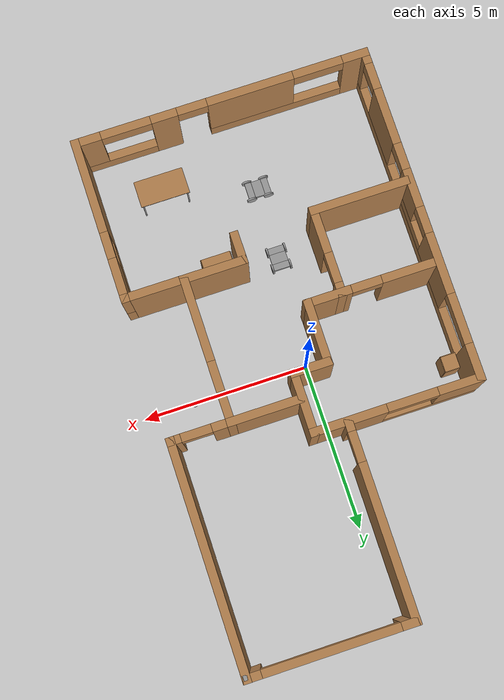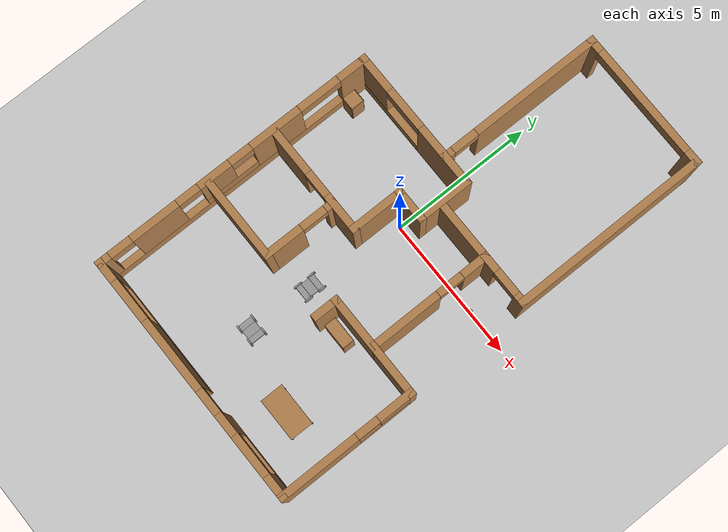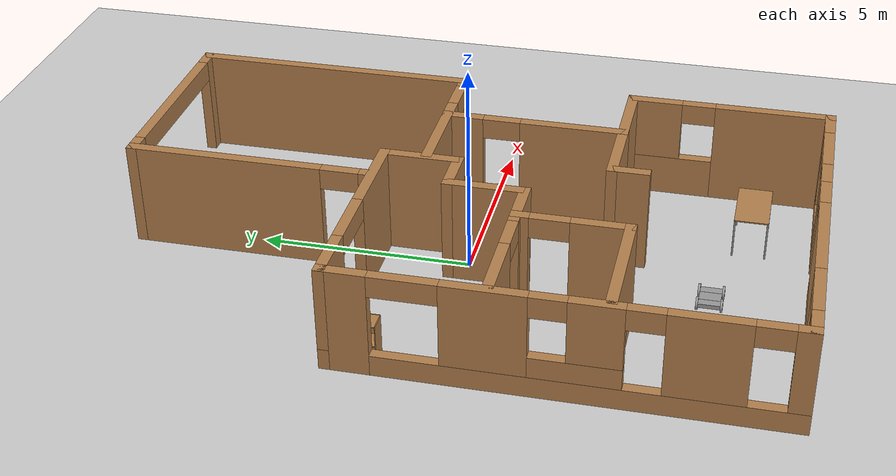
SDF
<sdf version="1.6">
 <world name="default">
  <plugin name="hello" filename="libhello.so"/>
  <light name="sun" type="directional">
   <pose>0 0 10 0 -0 0</pose>
   <diffuse>0.8 0.8 0.8 1</diffuse>
   <specular>0.1 0.1 0.1 1</specular>
   <attenuation>
    <range>1000</range>
    <constant>0.9</constant>
    <linear>0.01</linear>
    <quadratic>0.001</quadratic>
   </attenuation>
   <direction>-0.5 0.5 -1</direction>
  </light>
  <model name="ground_plane">
   <static>1</static>
   <link name="link">
    <collision name="collision">
     <geometry><plane><normal>0 0 1</normal><size>100 100</size></plane></geometry>
     <surface><friction><ode><mu>100</mu><mu2>50</mu2></ode></friction></surface>
    </collision>
    <visual name="visual">
     <cast_shadows>0</cast_shadows>
     <geometry><plane><normal>0 0 1</normal><size>100 100</size></plane></geometry>
     <material>
      <script><uri>file://media/materials/scripts/gazebo.material</uri><name>Gazebo/Grey</name></script>
     </material>
    </visual>
   </link>
  </model>
  <gravity>0 0 -9.8</gravity>
  <magnetic_field>6e-06 2.3e-05 -4.2e-05</magnetic_field>
  <atmosphere type="adiabatic"/>
  <physics name="default_physics" default="0" type="ode">
   <max_step_size>0.001</max_step_size>
   <real_time_factor>1</real_time_factor>
   <real_time_update_rate>1000</real_time_update_rate>
  </physics>
  <scene><ambient>0.4 0.4 0.4 1</ambient><background>0.7 0.7 0.7 1</background><shadows>1</shadows></scene>
  <spherical_coordinates>
   <surface_model>EARTH_WGS84</surface_model>
   <latitude_deg>0</latitude_deg>
   <longitude_deg>0</longitude_deg>
   <elevation>0</elevation>
   <heading_deg>0</heading_deg>
  </spherical_coordinates>
  <model name="mybuilding">
   <link name="Wall_0">
    <pose>1.95 7.875 0 0 -0 3.14159</pose>
    <visual name="Wall_0_Visual_0">
     <pose>-2.27407 0 1.25 0 -0 0</pose>
     <geometry><box><size>0.551856 0.25 2.5</size></box></geometry>
     <material>
      <script><uri>file://media/materials/scripts/gazebo.material</uri><name>Gazebo/Wood</name></script>
      <ambient>1 1 1 1</ambient>
     </material>
     <meta><layer>0</layer></meta>
    </visual>
    <collision name="Wall_0_Collision_0">
     <geometry><box><size>0.551856 0.25 2.5</size></box></geometry>
     <pose>-2.27407 0 1.25 0 -0 0</pose>
    </collision>
    <visual name="Wall_0_Visual_1">
     <pose>2.27593 0 1.25 0 -0 0</pose>
     <geometry><box><size>0.548144 0.25 2.5</size></box></geometry>
     <material>
      <script><uri>file://media/materials/scripts/gazebo.material</uri><name>Gazebo/Wood</name></script>
      <ambient>1 1 1 1</ambient>
     </material>
     <meta><layer>0</layer></meta>
    </visual>
    <collision name="Wall_0_Collision_1">
     <geometry><box><size>0.548144 0.25 2.5</size></box></geometry>
     <pose>2.27593 0 1.25 0 -0 0</pose>
    </collision>
    <visual name="Wall_0_Visual_2">
     <pose>0.001856 0 2.25 0 -0 0</pose>
     <geometry><box><size>4 0.25 0.5</size></box></geometry>
     <material>
      <script><uri>file://media/materials/scripts/gazebo.material</uri><name>Gazebo/Wood</name></script>
      <ambient>1 1 1 1</ambient>
     </material>
     <meta><layer>0</layer></meta>
    </visual>
    <collision name="Wall_0_Collision_2">
     <geometry><box><size>4 0.25 0.5</size></box></geometry>
     <pose>0.001856 0 2.25 0 -0 0</pose>
    </collision>
   </link>
   <link name="Wall_1">
    <pose>-0.475 5 0 0 0 -1.5708</pose>
    <visual name="Wall_1_Visual_0">
     <pose>-0.6625 0 1.25 0 -0 0</pose>
     <geometry><box><size>4.675 0.25 2.5</size></box></geometry>
     <material>
      <script><uri>file://media/materials/scripts/gazebo.material</uri><name>Gazebo/Wood</name></script>
      <ambient>1 1 1 1</ambient>
     </material>
     <meta><layer>0</layer></meta>
    </visual>
    <collision name="Wall_1_Collision_0">
     <geometry><box><size>4.675 0.25 2.5</size></box></geometry>
     <pose>-0.6625 0 1.25 0 -0 0</pose>
    </collision>
    <visual name="Wall_1_Visual_1">
     <pose>2.7875 0 1.25 0 -0 0</pose>
     <geometry><box><size>0.425 0.25 2.5</size></box></geometry>
     <material>
      <script><uri>file://media/materials/scripts/gazebo.material</uri><name>Gazebo/Wood</name></script>
      <ambient>1 1 1 1</ambient>
     </material>
     <meta><layer>0</layer></meta>
    </visual>
    <collision name="Wall_1_Collision_1">
     <geometry><box><size>0.425 0.25 2.5</size></box></geometry>
     <pose>2.7875 0 1.25 0 -0 0</pose>
    </collision>
    <visual name="Wall_1_Visual_2">
     <pose>2.125 0 2.25 0 -0 0</pose>
     <geometry><box><size>0.9 0.25 0.5</size></box></geometry>
     <material>
      <script><uri>file://media/materials/scripts/gazebo.material</uri><name>Gazebo/Wood</name></script>
      <ambient>1 1 1 1</ambient>
     </material>
     <meta><layer>0</layer></meta>
    </visual>
    <collision name="Wall_1_Collision_2">
     <geometry><box><size>0.9 0.25 0.5</size></box></geometry>
     <pose>2.125 0 2.25 0 -0 0</pose>
    </collision>
   </link>
   <link name="Wall_10">
    <pose>-4.375 -2.875 0 0 0 -1.5708</pose>
    <visual name="Wall_10_Visual_0">
     <pose>-4.56217 0 1.25 0 -0 0</pose>
     <geometry><box><size>1.12566 0.25 2.5</size></box></geometry>
     <material>
      <script><uri>file://media/materials/scripts/gazebo.material</uri><name>Gazebo/Wood</name></script>
      <ambient>1 1 1 1</ambient>
     </material>
     <meta><layer>0</layer></meta>
    </visual>
    <collision name="Wall_10_Collision_0">
     <geometry><box><size>1.12566 0.25 2.5</size></box></geometry>
     <pose>-4.56217 0 1.25 0 -0 0</pose>
    </collision>
    <visual name="Wall_10_Visual_1">
     <pose>0.562832 0 0.25 0 -0 0</pose>
     <geometry><box><size>9.12434 0.25 0.5</size></box></geometry>
     <material>
      <script><uri>file://media/materials/scripts/gazebo.material</uri><name>Gazebo/Wood</name></script>
      <ambient>1 1 1 1</ambient>
     </material>
     <meta><layer>0</layer></meta>
    </visual>
    <collision name="Wall_10_Collision_1">
     <geometry><box><size>9.12434 0.25 0.5</size></box></geometry>
     <pose>0.562832 0 0.25 0 -0 0</pose>
    </collision>
    <visual name="Wall_10_Visual_2">
     <pose>-1.57467 0 1.5 0 -0 0</pose>
     <geometry><box><size>1.84934 0.25 2</size></box></geometry>
     <material>
      <script><uri>file://media/materials/scripts/gazebo.material</uri><name>Gazebo/Wood</name></script>
      <ambient>1 1 1 1</ambient>
     </material>
     <meta><layer>0</layer></meta>
    </visual>
    <collision name="Wall_10_Collision_2">
     <geometry><box><size>1.84934 0.25 2</size></box></geometry>
     <pose>-1.57467 0 1.5 0 -0 0</pose>
    </collision>
    <visual name="Wall_10_Visual_3">
     <pose>2.98281 0 1.5 0 -0 0</pose>
     <geometry><box><size>1.72544 0.25 2</size></box></geometry>
     <material>
      <script><uri>file://media/materials/scripts/gazebo.material</uri><name>Gazebo/Wood</name></script>
      <ambient>1 1 1 1</ambient>
     </material>
     <meta><layer>0</layer></meta>
    </visual>
    <collision name="Wall_10_Collision_3">
     <geometry><box><size>1.72544 0.25 2</size></box></geometry>
     <pose>2.98281 0 1.5 0 -0 0</pose>
    </collision>
    <visual name="Wall_10_Visual_4">
     <pose>4.88526 0 1.5 0 -0 0</pose>
     <geometry><box><size>0.479475 0.25 2</size></box></geometry>
     <material>
      <script><uri>file://media/materials/scripts/gazebo.material</uri><name>Gazebo/Wood</name></script>
      <ambient>1 1 1 1</ambient>
     </material>
     <meta><layer>0</layer></meta>
    </visual>
    <collision name="Wall_10_Collision_4">
     <geometry><box><size>0.479475 0.25 2</size></box></geometry>
     <pose>4.88526 0 1.5 0 -0 0</pose>
    </collision>
    <visual name="Wall_10_Visual_5">
     <pose>0.335043 0 0.75 0 -0 0</pose>
     <geometry><box><size>1.97009 0.25 0.5</size></box></geometry>
     <material>
      <script><uri>file://media/materials/scripts/gazebo.material</uri><name>Gazebo/Wood</name></script>
      <ambient>1 1 1 1</ambient>
     </material>
     <meta><layer>0</layer></meta>
    </visual>
    <collision name="Wall_10_Collision_5">
     <geometry><box><size>1.97009 0.25 0.5</size></box></geometry>
     <pose>0.335043 0 0.75 0 -0 0</pose>
    </collision>
    <visual name="Wall_10_Visual_6">
     <pose>0.735043 0 1.75 0 -0 0</pose>
     <geometry><box><size>1.17009 0.25 1.5</size></box></geometry>
     <material>
      <script><uri>file://media/materials/scripts/gazebo.material</uri><name>Gazebo/Wood</name></script>
      <ambient>1 1 1 1</ambient>
     </material>
     <meta><layer>0</layer></meta>
    </visual>
    <collision name="Wall_10_Collision_6">
     <geometry><box><size>1.17009 0.25 1.5</size></box></geometry>
     <pose>0.735043 0 1.75 0 -0 0</pose>
    </collision>
    <visual name="Wall_10_Visual_7">
     <pose>-3.24934 0 2.25 0 -0 0</pose>
     <geometry><box><size>1.5 0.25 0.5</size></box></geometry>
     <material>
      <script><uri>file://media/materials/scripts/gazebo.material</uri><name>Gazebo/Wood</name></script>
      <ambient>1 1 1 1</ambient>
     </material>
     <meta><layer>0</layer></meta>
    </visual>
    <collision name="Wall_10_Collision_7">
     <geometry><box><size>1.5 0.25 0.5</size></box></geometry>
     <pose>-3.24934 0 2.25 0 -0 0</pose>
    </collision>
    <visual name="Wall_10_Visual_8">
     <pose>-0.25 0 2.25 0 -0 0</pose>
     <geometry><box><size>0.8 0.25 0.5</size></box></geometry>
     <material>
      <script><uri>file://media/materials/scripts/gazebo.material</uri><name>Gazebo/Wood</name></script>
      <ambient>1 1 1 1</ambient>
     </material>
     <meta><layer>0</layer></meta>
    </visual>
    <collision name="Wall_10_Collision_8">
     <geometry><box><size>0.8 0.25 0.5</size></box></geometry>
     <pose>-0.25 0 2.25 0 -0 0</pose>
    </collision>
    <visual name="Wall_10_Visual_9">
     <pose>4.24552 0 2.25 0 -0 0</pose>
     <geometry><box><size>0.8 0.25 0.5</size></box></geometry>
     <material>
      <script><uri>file://media/materials/scripts/gazebo.material</uri><name>Gazebo/Wood</name></script>
      <ambient>1 1 1 1</ambient>
     </material>
     <meta><layer>0</layer></meta>
    </visual>
    <collision name="Wall_10_Collision_9">
     <geometry><box><size>0.8 0.25 0.5</size></box></geometry>
     <pose>4.24552 0 2.25 0 -0 0</pose>
    </collision>
    <visual name="Wall_10_Visual_10">
     <pose>1.72009 0 2.25 0 -0 0</pose>
     <geometry><box><size>0.8 0.25 0.5</size></box></geometry>
     <material>
      <script><uri>file://media/materials/scripts/gazebo.material</uri><name>Gazebo/Wood</name></script>
      <ambient>1 1 1 1</ambient>
     </material>
     <meta><layer>0</layer></meta>
    </visual>
    <collision name="Wall_10_Collision_10">
     <geometry><box><size>0.8 0.25 0.5</size></box></geometry>
     <pose>1.72009 0 2.25 0 -0 0</pose>
    </collision>
   </link>
   <link name="Wall_11">
    <pose>0 -7.875 0 0 -0 0</pose>
    <visual name="Wall_11_Visual_0">
     <pose>-4.09506 0 1.25 0 -0 0</pose>
     <geometry><box><size>0.809873 0.25 2.5</size></box></geometry>
     <material>
      <script><uri>file://media/materials/scripts/gazebo.material</uri><name>Gazebo/Wood</name></script>
      <ambient>1 1 1 1</ambient>
     </material>
     <meta><layer>0</layer></meta>
    </visual>
    <collision name="Wall_11_Collision_0">
     <geometry><box><size>0.809873 0.25 2.5</size></box></geometry>
     <pose>-4.09506 0 1.25 0 -0 0</pose>
    </collision>
    <visual name="Wall_11_Visual_1">
     <pose>1.7214 0 1.25 0 -0 0</pose>
     <geometry><box><size>0.792805 0.25 2.5</size></box></geometry>
     <material>
      <script><uri>file://media/materials/scripts/gazebo.material</uri><name>Gazebo/Wood</name></script>
      <ambient>1 1 1 1</ambient>
     </material>
     <meta><layer>0</layer></meta>
    </visual>
    <collision name="Wall_11_Collision_1">
     <geometry><box><size>0.792805 0.25 2.5</size></box></geometry>
     <pose>1.7214 0 1.25 0 -0 0</pose>
    </collision>
    <visual name="Wall_11_Visual_2">
     <pose>-1.63256 0 0.25 0 -0 0</pose>
     <geometry><box><size>4.11513 0.25 0.5</size></box></geometry>
     <material>
      <script><uri>file://media/materials/scripts/gazebo.material</uri><name>Gazebo/Wood</name></script>
      <ambient>1 1 1 1</ambient>
     </material>
     <meta><layer>0</layer></meta>
    </visual>
    <collision name="Wall_11_Collision_2">
     <geometry><box><size>4.11513 0.25 0.5</size></box></geometry>
     <pose>-1.63256 0 0.25 0 -0 0</pose>
    </collision>
    <visual name="Wall_11_Visual_3">
     <pose>3.3089 0 0.25 0 -0 0</pose>
     <geometry><box><size>2.38219 0.25 0.5</size></box></geometry>
     <material>
      <script><uri>file://media/materials/scripts/gazebo.material</uri><name>Gazebo/Wood</name></script>
      <ambient>1 1 1 1</ambient>
     </material>
     <meta><layer>0</layer></meta>
    </visual>
    <collision name="Wall_11_Collision_3">
     <geometry><box><size>2.38219 0.25 0.5</size></box></geometry>
     <pose>3.3089 0 0.25 0 -0 0</pose>
    </collision>
    <visual name="Wall_11_Visual_4">
     <pose>-0.882564 0 1.5 0 -0 0</pose>
     <geometry><box><size>2.61513 0.25 2</size></box></geometry>
     <material>
      <script><uri>file://media/materials/scripts/gazebo.material</uri><name>Gazebo/Wood</name></script>
      <ambient>1 1 1 1</ambient>
     </material>
     <meta><layer>0</layer></meta>
    </visual>
    <collision name="Wall_11_Collision_4">
     <geometry><box><size>2.61513 0.25 2</size></box></geometry>
     <pose>-0.882564 0 1.5 0 -0 0</pose>
    </collision>
    <visual name="Wall_11_Visual_5">
     <pose>-0.882564 0 1.5 0 -0 0</pose>
     <geometry><box><size>2.61513 0.25 2</size></box></geometry>
     <material>
      <script><uri>file://media/materials/scripts/gazebo.material</uri><name>Gazebo/Wood</name></script>
      <ambient>1 1 1 1</ambient>
     </material>
     <meta><layer>0</layer></meta>
    </visual>
    <collision name="Wall_11_Collision_5">
     <geometry><box><size>2.61513 0.25 2</size></box></geometry>
     <pose>-0.882564 0 1.5 0 -0 0</pose>
    </collision>
    <visual name="Wall_11_Visual_6">
     <pose>4.0589 0 1.5 0 -0 0</pose>
     <geometry><box><size>0.882195 0.25 2</size></box></geometry>
     <material>
      <script><uri>file://media/materials/scripts/gazebo.material</uri><name>Gazebo/Wood</name></script>
      <ambient>1 1 1 1</ambient>
     </material>
     <meta><layer>0</layer></meta>
    </visual>
    <collision name="Wall_11_Collision_6">
     <geometry><box><size>0.882195 0.25 2</size></box></geometry>
     <pose>4.0589 0 1.5 0 -0 0</pose>
    </collision>
    <visual name="Wall_11_Visual_7">
     <pose>-2.94013 0 2.25 0 -0 0</pose>
     <geometry><box><size>1.5 0.25 0.5</size></box></geometry>
     <material>
      <script><uri>file://media/materials/scripts/gazebo.material</uri><name>Gazebo/Wood</name></script>
      <ambient>1 1 1 1</ambient>
     </material>
     <meta><layer>0</layer></meta>
    </visual>
    <collision name="Wall_11_Collision_7">
     <geometry><box><size>1.5 0.25 0.5</size></box></geometry>
     <pose>-2.94013 0 2.25 0 -0 0</pose>
    </collision>
    <visual name="Wall_11_Visual_8">
     <pose>2.86781 0 2.25 0 -0 0</pose>
     <geometry><box><size>1.5 0.25 0.5</size></box></geometry>
     <material>
      <script><uri>file://media/materials/scripts/gazebo.material</uri><name>Gazebo/Wood</name></script>
      <ambient>1 1 1 1</ambient>
     </material>
     <meta><layer>0</layer></meta>
    </visual>
    <collision name="Wall_11_Collision_8">
     <geometry><box><size>1.5 0.25 0.5</size></box></geometry>
     <pose>2.86781 0 2.25 0 -0 0</pose>
    </collision>
    <visual name="Wall_11_Visual_9">
     <pose>0.875 0 2.25 0 -0 0</pose>
     <geometry><box><size>0.9 0.25 0.5</size></box></geometry>
     <material>
      <script><uri>file://media/materials/scripts/gazebo.material</uri><name>Gazebo/Wood</name></script>
      <ambient>1 1 1 1</ambient>
     </material>
     <meta><layer>0</layer></meta>
    </visual>
    <collision name="Wall_11_Collision_9">
     <geometry><box><size>0.9 0.25 0.5</size></box></geometry>
     <pose>0.875 0 2.25 0 -0 0</pose>
    </collision>
    <visual name="Wall_11_Visual_10">
     <pose>0.875 0 2.25 0 -0 0</pose>
     <geometry><box><size>0.9 0.25 0.5</size></box></geometry>
     <material>
      <script><uri>file://media/materials/scripts/gazebo.material</uri><name>Gazebo/Wood</name></script>
      <ambient>1 1 1 1</ambient>
     </material>
     <meta><layer>0</layer></meta>
    </visual>
    <collision name="Wall_11_Collision_10">
     <geometry><box><size>0.9 0.25 0.5</size></box></geometry>
     <pose>0.875 0 2.25 0 -0 0</pose>
    </collision>
   </link>
   <link name="Wall_12">
    <pose>4.375 -5.5 0 0 -0 1.5708</pose>
    <visual name="Wall_12_Visual_0">
     <pose>-1.06859 0 1.25 0 -0 0</pose>
     <geometry><box><size>2.86282 0.25 2.5</size></box></geometry>
     <material>
      <script><uri>file://media/materials/scripts/gazebo.material</uri><name>Gazebo/Wood</name></script>
      <ambient>1 1 1 1</ambient>
     </material>
     <meta><layer>0</layer></meta>
    </visual>
    <collision name="Wall_12_Collision_0">
     <geometry><box><size>2.86282 0.25 2.5</size></box></geometry>
     <pose>-1.06859 0 1.25 0 -0 0</pose>
    </collision>
    <visual name="Wall_12_Visual_1">
     <pose>1.43141 0 0.5 0 -0 0</pose>
     <geometry><box><size>2.13718 0.25 1</size></box></geometry>
     <material>
      <script><uri>file://media/materials/scripts/gazebo.material</uri><name>Gazebo/Wood</name></script>
      <ambient>1 1 1 1</ambient>
     </material>
     <meta><layer>0</layer></meta>
    </visual>
    <collision name="Wall_12_Collision_1">
     <geometry><box><size>2.13718 0.25 1</size></box></geometry>
     <pose>1.43141 0 0.5 0 -0 0</pose>
    </collision>
    <visual name="Wall_12_Visual_2">
     <pose>1.83141 0 1.75 0 -0 0</pose>
     <geometry><box><size>1.33718 0.25 1.5</size></box></geometry>
     <material>
      <script><uri>file://media/materials/scripts/gazebo.material</uri><name>Gazebo/Wood</name></script>
      <ambient>1 1 1 1</ambient>
     </material>
     <meta><layer>0</layer></meta>
    </visual>
    <collision name="Wall_12_Collision_2">
     <geometry><box><size>1.33718 0.25 1.5</size></box></geometry>
     <pose>1.83141 0 1.75 0 -0 0</pose>
    </collision>
    <visual name="Wall_12_Visual_3">
     <pose>0.762824 0 2.25 0 -0 0</pose>
     <geometry><box><size>0.8 0.25 0.5</size></box></geometry>
     <material>
      <script><uri>file://media/materials/scripts/gazebo.material</uri><name>Gazebo/Wood</name></script>
      <ambient>1 1 1 1</ambient>
     </material>
     <meta><layer>0</layer></meta>
    </visual>
    <collision name="Wall_12_Collision_3">
     <geometry><box><size>0.8 0.25 0.5</size></box></geometry>
     <pose>0.762824 0 2.25 0 -0 0</pose>
    </collision>
   </link>
   <link name="Wall_13">
    <collision name="Wall_13_Collision">
     <geometry><box><size>2 0.25 2.5</size></box></geometry>
     <pose>0 0 1.25 0 -0 0</pose>
    </collision>
    <visual name="Wall_13_Visual">
     <pose>0 0 1.25 0 -0 0</pose>
     <geometry><box><size>2 0.25 2.5</size></box></geometry>
     <material>
      <script><uri>file://media/materials/scripts/gazebo.material</uri><name>Gazebo/Wood</name></script>
      <ambient>1 1 1 1</ambient>
     </material>
     <meta><layer>0</layer></meta>
    </visual>
    <pose>3.5 -3.125 0 0 -0 3.14159</pose>
   </link>
   <link name="Wall_14">
    <pose>2.625 -1 0 0 -0 1.5708</pose>
    <visual name="Wall_14_Visual_0">
     <pose>-0.957655 0 1.25 0 -0 0</pose>
     <geometry><box><size>2.58469 0.25 2.5</size></box></geometry>
     <material>
      <script><uri>file://media/materials/scripts/gazebo.material</uri><name>Gazebo/Wood</name></script>
      <ambient>1 1 1 1</ambient>
     </material>
     <meta><layer>0</layer></meta>
    </visual>
    <collision name="Wall_14_Collision_0">
     <geometry><box><size>2.58469 0.25 2.5</size></box></geometry>
     <pose>-0.957655 0 1.25 0 -0 0</pose>
    </collision>
    <visual name="Wall_14_Visual_1">
     <pose>1.74235 0 1.25 0 -0 0</pose>
     <geometry><box><size>1.01531 0.25 2.5</size></box></geometry>
     <material>
      <script><uri>file://media/materials/scripts/gazebo.material</uri><name>Gazebo/Wood</name></script>
      <ambient>1 1 1 1</ambient>
     </material>
     <meta><layer>0</layer></meta>
    </visual>
    <collision name="Wall_14_Collision_1">
     <geometry><box><size>1.01531 0.25 2.5</size></box></geometry>
     <pose>1.74235 0 1.25 0 -0 0</pose>
    </collision>
    <visual name="Wall_14_Visual_2">
     <pose>0.78469 0 2.25 0 -0 0</pose>
     <geometry><box><size>0.9 0.25 0.5</size></box></geometry>
     <material>
      <script><uri>file://media/materials/scripts/gazebo.material</uri><name>Gazebo/Wood</name></script>
      <ambient>1 1 1 1</ambient>
     </material>
     <meta><layer>0</layer></meta>
    </visual>
    <collision name="Wall_14_Collision_2">
     <geometry><box><size>0.9 0.25 0.5</size></box></geometry>
     <pose>0.78469 0 2.25 0 -0 0</pose>
    </collision>
   </link>
   <link name="Wall_153">
    <pose>-1.475 -2.625 0 0 0 -1.5708</pose>
    <visual name="Wall_153_Visual_0">
     <pose>-1.1625 0 1.25 0 -0 0</pose>
     <geometry><box><size>0.425 0.25 2.5</size></box></geometry>
     <material>
      <script><uri>file://media/materials/scripts/gazebo.material</uri><name>Gazebo/Wood</name></script>
      <ambient>1 1 1 1</ambient>
     </material>
     <meta><layer>0</layer></meta>
    </visual>
    <collision name="Wall_153_Collision_0">
     <geometry><box><size>0.425 0.25 2.5</size></box></geometry>
     <pose>-1.1625 0 1.25 0 -0 0</pose>
    </collision>
    <visual name="Wall_153_Visual_1">
     <pose>0.6625 0 1.25 0 -0 0</pose>
     <geometry><box><size>1.425 0.25 2.5</size></box></geometry>
     <material>
      <script><uri>file://media/materials/scripts/gazebo.material</uri><name>Gazebo/Wood</name></script>
      <ambient>1 1 1 1</ambient>
     </material>
     <meta><layer>0</layer></meta>
    </visual>
    <collision name="Wall_153_Collision_1">
     <geometry><box><size>1.425 0.25 2.5</size></box></geometry>
     <pose>0.6625 0 1.25 0 -0 0</pose>
    </collision>
    <visual name="Wall_153_Visual_2">
     <pose>-0.5 0 2.25 0 -0 0</pose>
     <geometry><box><size>0.9 0.25 0.5</size></box></geometry>
     <material>
      <script><uri>file://media/materials/scripts/gazebo.material</uri><name>Gazebo/Wood</name></script>
      <ambient>1 1 1 1</ambient>
     </material>
     <meta><layer>0</layer></meta>
    </visual>
    <collision name="Wall_153_Collision_2">
     <geometry><box><size>0.9 0.25 0.5</size></box></geometry>
     <pose>-0.5 0 2.25 0 -0 0</pose>
    </collision>
   </link>
   <link name="Wall_154">
    <collision name="Wall_154_Collision">
     <geometry><box><size>3 0.25 2.5</size></box></geometry>
     <pose>0 0 1.25 0 -0 0</pose>
    </collision>
    <visual name="Wall_154_Visual">
     <pose>0 0 1.25 0 -0 0</pose>
     <geometry><box><size>3 0.25 2.5</size></box></geometry>
     <material>
      <script><uri>file://media/materials/scripts/gazebo.material</uri><name>Gazebo/Wood</name></script>
      <ambient>1 1 1 1</ambient>
     </material>
     <meta><layer>0</layer></meta>
    </visual>
    <pose>-2.85 -3.875 0 0 -0 3.14159</pose>
   </link>
   <link name="Wall_156">
    <collision name="Wall_156_Collision">
     <geometry><box><size>2 0.25 2.5</size></box></geometry>
     <pose>0 0 1.25 0 -0 0</pose>
    </collision>
    <visual name="Wall_156_Visual">
     <pose>0 0 1.25 0 -0 0</pose>
     <geometry><box><size>2 0.25 2.5</size></box></geometry>
     <material>
      <script><uri>file://media/materials/scripts/gazebo.material</uri><name>Gazebo/Wood</name></script>
      <ambient>1 1 1 1</ambient>
     </material>
     <meta><layer>0</layer></meta>
    </visual>
    <pose>1.75 -3.125 0 0 -0 3.14159</pose>
   </link>
   <link name="Wall_157">
    <collision name="Wall_157_Collision">
     <geometry><box><size>1 0.25 2.5</size></box></geometry>
     <pose>0 0 1.25 0 -0 0</pose>
    </collision>
    <visual name="Wall_157_Visual">
     <pose>0 0 1.25 0 -0 0</pose>
     <geometry><box><size>1 0.25 2.5</size></box></geometry>
     <material>
      <script><uri>file://media/materials/scripts/gazebo.material</uri><name>Gazebo/Wood</name></script>
      <ambient>1 1 1 1</ambient>
     </material>
     <meta><layer>0</layer></meta>
    </visual>
    <pose>0.875 -3.5 0 0 0 -1.5708</pose>
   </link>
   <link name="Wall_16">
    <collision name="Wall_16_Collision">
     <geometry><box><size>7 0.25 2.5</size></box></geometry>
     <pose>0 0 1.25 0 -0 0</pose>
    </collision>
    <visual name="Wall_16_Visual">
     <pose>0 0 1.25 0 -0 0</pose>
     <geometry><box><size>7 0.25 2.5</size></box></geometry>
     <material>
      <script><uri>file://media/materials/scripts/gazebo.material</uri><name>Gazebo/Wood</name></script>
      <ambient>1 1 1 1</ambient>
     </material>
     <meta><layer>0</layer></meta>
    </visual>
    <pose>4.375 4.5 0 0 -0 1.5708</pose>
   </link>
   <link name="Wall_17">
    <collision name="Wall_17_Collision">
     <geometry><box><size>0.15 0.15 2.5</size></box></geometry>
     <pose>0 0 1.25 0 -0 0</pose>
    </collision>
    <visual name="Wall_17_Visual">
     <pose>0 0 1.25 0 -0 0</pose>
     <geometry><box><size>0.15 0.15 2.5</size></box></geometry>
     <material>
      <script><uri>file://media/materials/scripts/gazebo.material</uri><name>Gazebo/Grey</name></script>
      <ambient>1 1 1 1</ambient>
     </material>
     <meta><layer>0</layer></meta>
    </visual>
    <pose>4.375 7.83421 0 0 -0 0</pose>
   </link>
   <link name="Wall_18">
    <collision name="Wall_18_Collision">
     <geometry><box><size>0.15 0.15 2.5</size></box></geometry>
     <pose>0 0 1.25 0 -0 0</pose>
    </collision>
    <visual name="Wall_18_Visual">
     <pose>0 0 1.25 0 -0 0</pose>
     <geometry><box><size>0.15 0.15 2.5</size></box></geometry>
     <material>
      <script><uri>file://media/materials/scripts/gazebo.material</uri><name>Gazebo/Grey</name></script>
      <ambient>1 1 1 1</ambient>
     </material>
     <meta><layer>0</layer></meta>
    </visual>
    <pose>4.375 7.83421 0 0 -0 0</pose>
   </link>
   <link name="Wall_20">
    <collision name="Wall_20_Collision">
     <geometry><box><size>2 0.25 2.5</size></box></geometry>
     <pose>0 0 1.25 0 -0 0</pose>
    </collision>
    <visual name="Wall_20_Visual">
     <pose>0 0 1.25 0 -0 0</pose>
     <geometry><box><size>2 0.25 2.5</size></box></geometry>
     <material>
      <script><uri>file://media/materials/scripts/gazebo.material</uri><name>Gazebo/Wood</name></script>
      <ambient>1 1 1 1</ambient>
     </material>
     <meta><layer>0</layer></meta>
    </visual>
    <pose>0.525 1.25 0 0 0 -1.5708</pose>
   </link>
   <link name="Wall_22">
    <collision name="Wall_22_Collision">
     <geometry><box><size>2.25 0.25 2.5</size></box></geometry>
     <pose>0 0 1.25 0 -0 0</pose>
    </collision>
    <visual name="Wall_22_Visual">
     <pose>0 0 1.25 0 -0 0</pose>
     <geometry><box><size>2.25 0.25 2.5</size></box></geometry>
     <material>
      <script><uri>file://media/materials/scripts/gazebo.material</uri><name>Gazebo/Wood</name></script>
      <ambient>1 1 1 1</ambient>
     </material>
     <meta><layer>0</layer></meta>
    </visual>
    <pose>1.625 1.125 0 0 -0 3.14159</pose>
   </link>
   <link name="Wall_24">
    <pose>3.5 1.125 0 0 -0 3.14159</pose>
    <visual name="Wall_24_Visual_0">
     <pose>-0.7875 0 1.25 0 -0 0</pose>
     <geometry><box><size>0.425 0.25 2.5</size></box></geometry>
     <material>
      <script><uri>file://media/materials/scripts/gazebo.material</uri><name>Gazebo/Wood</name></script>
      <ambient>1 1 1 1</ambient>
     </material>
     <meta><layer>0</layer></meta>
    </visual>
    <collision name="Wall_24_Collision_0">
     <geometry><box><size>0.425 0.25 2.5</size></box></geometry>
     <pose>-0.7875 0 1.25 0 -0 0</pose>
    </collision>
    <visual name="Wall_24_Visual_1">
     <pose>0.6625 0 1.25 0 -0 0</pose>
     <geometry><box><size>0.675 0.25 2.5</size></box></geometry>
     <material>
      <script><uri>file://media/materials/scripts/gazebo.material</uri><name>Gazebo/Wood</name></script>
      <ambient>1 1 1 1</ambient>
     </material>
     <meta><layer>0</layer></meta>
    </visual>
    <collision name="Wall_24_Collision_1">
     <geometry><box><size>0.675 0.25 2.5</size></box></geometry>
     <pose>0.6625 0 1.25 0 -0 0</pose>
    </collision>
    <visual name="Wall_24_Visual_2">
     <pose>-0.125 0 2.25 0 -0 0</pose>
     <geometry><box><size>0.9 0.25 0.5</size></box></geometry>
     <material>
      <script><uri>file://media/materials/scripts/gazebo.material</uri><name>Gazebo/Wood</name></script>
      <ambient>1 1 1 1</ambient>
     </material>
     <meta><layer>0</layer></meta>
    </visual>
    <collision name="Wall_24_Collision_2">
     <geometry><box><size>0.9 0.25 0.5</size></box></geometry>
     <pose>-0.125 0 2.25 0 -0 0</pose>
    </collision>
   </link>
   <link name="Wall_41">
    <collision name="Wall_41_Collision">
     <geometry><box><size>1.25 0.25 2.5</size></box></geometry>
     <pose>0 0 1.25 0 -0 0</pose>
    </collision>
    <visual name="Wall_41_Visual">
     <pose>0 0 1.25 0 -0 0</pose>
     <geometry><box><size>1.25 0.25 2.5</size></box></geometry>
     <material>
      <script><uri>file://media/materials/scripts/gazebo.material</uri><name>Gazebo/Wood</name></script>
      <ambient>1 1 1 1</ambient>
     </material>
     <meta><layer>0</layer></meta>
    </visual>
    <pose>0.025 0.375 0 0 -0 3.14159</pose>
   </link>
   <link name="Wall_42">
    <collision name="Wall_42_Collision">
     <geometry><box><size>2 0.25 2.5</size></box></geometry>
     <pose>0 0 1.25 0 -0 0</pose>
    </collision>
    <visual name="Wall_42_Visual">
     <pose>0 0 1.25 0 -0 0</pose>
     <geometry><box><size>2 0.25 2.5</size></box></geometry>
     <material>
      <script><uri>file://media/materials/scripts/gazebo.material</uri><name>Gazebo/Wood</name></script>
      <ambient>1 1 1 1</ambient>
     </material>
     <meta><layer>0</layer></meta>
    </visual>
    <pose>-0.475 -0.5 0 0 0 -1.5708</pose>
   </link>
   <link name="Wall_43">
    <pose>-2.35 -1.375 0 0 -0 3.14159</pose>
    <visual name="Wall_43_Visual_0">
     <pose>-1.29229 0 1.25 0 -0 0</pose>
     <geometry><box><size>1.41542 0.25 2.5</size></box></geometry>
     <material>
      <script><uri>file://media/materials/scripts/gazebo.material</uri><name>Gazebo/Wood</name></script>
      <ambient>1 1 1 1</ambient>
     </material>
     <meta><layer>0</layer></meta>
    </visual>
    <collision name="Wall_43_Collision_0">
     <geometry><box><size>1.41542 0.25 2.5</size></box></geometry>
     <pose>-1.29229 0 1.25 0 -0 0</pose>
    </collision>
    <visual name="Wall_43_Visual_1">
     <pose>1.15771 0 1.25 0 -0 0</pose>
     <geometry><box><size>1.68457 0.25 2.5</size></box></geometry>
     <material>
      <script><uri>file://media/materials/scripts/gazebo.material</uri><name>Gazebo/Wood</name></script>
      <ambient>1 1 1 1</ambient>
     </material>
     <meta><layer>0</layer></meta>
    </visual>
    <collision name="Wall_43_Collision_1">
     <geometry><box><size>1.68457 0.25 2.5</size></box></geometry>
     <pose>1.15771 0 1.25 0 -0 0</pose>
    </collision>
    <visual name="Wall_43_Visual_2">
     <pose>-0.134575 0 2.25 0 -0 0</pose>
     <geometry><box><size>0.9 0.25 0.5</size></box></geometry>
     <material>
      <script><uri>file://media/materials/scripts/gazebo.material</uri><name>Gazebo/Wood</name></script>
      <ambient>1 1 1 1</ambient>
     </material>
     <meta><layer>0</layer></meta>
    </visual>
    <collision name="Wall_43_Collision_2">
     <geometry><box><size>0.9 0.25 0.5</size></box></geometry>
     <pose>-0.134575 0 2.25 0 -0 0</pose>
    </collision>
   </link>
   <link name="Wall_9">
    <pose>-1.925 2.125 0 0 -0 3.14159</pose>
    <visual name="Wall_9_Visual_0">
     <pose>-1.4375 0 1.25 0 -0 0</pose>
     <geometry><box><size>2.275 0.25 2.5</size></box></geometry>
     <material>
      <script><uri>file://media/materials/scripts/gazebo.material</uri><name>Gazebo/Wood</name></script>
      <ambient>1 1 1 1</ambient>
     </material>
     <meta><layer>0</layer></meta>
    </visual>
    <collision name="Wall_9_Collision_0">
     <geometry><box><size>2.275 0.25 2.5</size></box></geometry>
     <pose>-1.4375 0 1.25 0 -0 0</pose>
    </collision>
    <visual name="Wall_9_Visual_1">
     <pose>1.1375 0 0.25 0 -0 0</pose>
     <geometry><box><size>2.875 0.25 0.5</size></box></geometry>
     <material>
      <script><uri>file://media/materials/scripts/gazebo.material</uri><name>Gazebo/Wood</name></script>
      <ambient>1 1 1 1</ambient>
     </material>
     <meta><layer>0</layer></meta>
    </visual>
    <collision name="Wall_9_Collision_1">
     <geometry><box><size>2.875 0.25 0.5</size></box></geometry>
     <pose>1.1375 0 0.25 0 -0 0</pose>
    </collision>
    <visual name="Wall_9_Visual_2">
     <pose>1.8875 0 1.5 0 -0 0</pose>
     <geometry><box><size>1.375 0.25 2</size></box></geometry>
     <material>
      <script><uri>file://media/materials/scripts/gazebo.material</uri><name>Gazebo/Wood</name></script>
      <ambient>1 1 1 1</ambient>
     </material>
     <meta><layer>0</layer></meta>
    </visual>
    <collision name="Wall_9_Collision_2">
     <geometry><box><size>1.375 0.25 2</size></box></geometry>
     <pose>1.8875 0 1.5 0 -0 0</pose>
    </collision>
    <visual name="Wall_9_Visual_3">
     <pose>0.45 0 2.25 0 -0 0</pose>
     <geometry><box><size>1.5 0.25 0.5</size></box></geometry>
     <material>
      <script><uri>file://media/materials/scripts/gazebo.material</uri><name>Gazebo/Wood</name></script>
      <ambient>1 1 1 1</ambient>
     </material>
     <meta><layer>0</layer></meta>
    </visual>
    <collision name="Wall_9_Collision_3">
     <geometry><box><size>1.5 0.25 0.5</size></box></geometry>
     <pose>0.45 0 2.25 0 -0 0</pose>
    </collision>
   </link>
   <static>1</static>
  </model>
  <model name="table">
   <static>1</static>
   <link name="link">
    <collision name="surface">
     <pose>0 0 1 0 -0 0</pose>
     <geometry><box><size>1.5 0.8 0.03</size></box></geometry>
     <surface><friction><ode><mu>0.6</mu><mu2>0.6</mu2></ode></friction></surface>
    </collision>
    <visual name="visual1">
     <pose>0 0 1 0 -0 0</pose>
     <geometry><box><size>1.5 0.8 0.03</size></box></geometry>
     <material>
      <script><uri>file://media/materials/scripts/gazebo.material</uri><name>Gazebo/Wood</name></script>
     </material>
    </visual>
    <collision name="front_left_leg">
     <pose>0.68 0.38 0.5 0 -0 0</pose>
     <geometry><cylinder><radius>0.02</radius><length>1</length></cylinder></geometry>
    </collision>
    <visual name="front_left_leg">
     <pose>0.68 0.38 0.5 0 -0 0</pose>
     <geometry><cylinder><radius>0.02</radius><length>1</length></cylinder></geometry>
     <material>
      <script><uri>file://media/materials/scripts/gazebo.material</uri><name>Gazebo/Grey</name></script>
     </material>
    </visual>
    <collision name="front_right_leg">
     <pose>0.68 -0.38 0.5 0 -0 0</pose>
     <geometry><cylinder><radius>0.02</radius><length>1</length></cylinder></geometry>
    </collision>
    <visual name="front_right_leg">
     <pose>0.68 -0.38 0.5 0 -0 0</pose>
     <geometry><cylinder><radius>0.02</radius><length>1</length></cylinder></geometry>
     <material>
      <script><uri>file://media/materials/scripts/gazebo.material</uri><name>Gazebo/Grey</name></script>
     </material>
    </visual>
    <collision name="back_right_leg">
     <pose>-0.68 -0.38 0.5 0 -0 0</pose>
     <geometry><cylinder><radius>0.02</radius><length>1</length></cylinder></geometry>
    </collision>
    <visual name="back_right_leg">
     <pose>-0.68 -0.38 0.5 0 -0 0</pose>
     <geometry><cylinder><radius>0.02</radius><length>1</length></cylinder></geometry>
     <material>
      <script><uri>file://media/materials/scripts/gazebo.material</uri><name>Gazebo/Grey</name></script>
     </material>
    </visual>
    <collision name="back_left_leg">
     <pose>-0.68 0.38 0.5 0 -0 0</pose>
     <geometry><cylinder><radius>0.02</radius><length>1</length></cylinder></geometry>
    </collision>
    <visual name="back_left_leg">
     <pose>-0.68 0.38 0.5 0 -0 0</pose>
     <geometry><cylinder><radius>0.02</radius><length>1</length></cylinder></geometry>
     <material>
      <script><uri>file://media/materials/scripts/gazebo.material</uri><name>Gazebo/Grey</name></script>
     </material>
    </visual>
   </link>
   <pose>2.40079 -6.32135 0 0 -0 0</pose>
  </model>
  <model name="cabinet">
   <static>1</static>
   <link name="cabinet_bottom_plate">
    <inertial>
     <pose>0 0 -1 0 -0 0</pose>
     <inertia><ixx>2.05</ixx><ixy>0</ixy><ixz>0</ixz><iyy>2.05</iyy><iyz>0</iyz><izz>2.05</izz></inertia>
     <mass>25</mass>
    </inertial>
    <collision name="cabinet_bottom_plate_geom">
     <pose>0 0 0.01 0 -0 0</pose>
     <geometry><box><size>0.45 0.45 0.02</size></box></geometry>
    </collision>
    <visual name="cabinet_bottom_plate_geom_visual">
     <pose>0 0 0.01 0 -0 0</pose>
     <geometry><box><size>0.45 0.45 0.02</size></box></geometry>
     <material>
      <script><uri>file://media/materials/scripts/gazebo.material</uri><name>Gazebo/Wood</name></script>
     </material>
    </visual>
    <collision name="cabinet_bottom_plate_geom_cabinet_back_plate">
     <pose>0.235 0 0.51 0 -0 0</pose>
     <geometry><box><size>0.02 0.45 1.02</size></box></geometry>
    </collision>
    <visual name="cabinet_bottom_plate_geom_cabinet_back_plate_visual">
     <pose>0.235 0 0.51 0 -0 0</pose>
     <geometry><box><size>0.02 0.45 1.02</size></box></geometry>
     <material>
      <script><uri>file://media/materials/scripts/gazebo.material</uri><name>Gazebo/Wood</name></script>
     </material>
    </visual>
    <collision name="cabinet_bottom_plate_geom_cabinet_left_plate">
     <pose>0 0.235 0.51 0 -0 0</pose>
     <geometry><box><size>0.45 0.02 1.02</size></box></geometry>
    </collision>
    <visual name="cabinet_bottom_plate_geom_cabinet_left_plate_visual">
     <pose>0 0.235 0.51 0 -0 0</pose>
     <geometry><box><size>0.45 0.02 1.02</size></box></geometry>
     <material>
      <script><uri>file://media/materials/scripts/gazebo.material</uri><name>Gazebo/Wood</name></script>
     </material>
    </visual>
    <collision name="cabinet_bottom_plate_geom_cabinet_middle_plate">
     <pose>0 0 0.51 0 -0 0</pose>
     <geometry><box><size>0.45 0.45 0.02</size></box></geometry>
    </collision>
    <visual name="cabinet_bottom_plate_geom_cabinet_middle_plate_visual">
     <pose>0 0 0.51 0 -0 0</pose>
     <geometry><box><size>0.45 0.45 0.02</size></box></geometry>
     <material>
      <script><uri>file://media/materials/scripts/gazebo.material</uri><name>Gazebo/Wood</name></script>
     </material>
    </visual>
    <collision name="cabinet_bottom_plate_geom_cabinet_right_plate">
     <pose>0 -0.235 0.51 0 -0 0</pose>
     <geometry><box><size>0.45 0.02 1.02</size></box></geometry>
    </collision>
    <visual name="cabinet_bottom_plate_geom_cabinet_right_plate_visual">
     <pose>0 -0.235 0.51 0 -0 0</pose>
     <geometry><box><size>0.45 0.02 1.02</size></box></geometry>
     <material>
      <script><uri>file://media/materials/scripts/gazebo.material</uri><name>Gazebo/Wood</name></script>
     </material>
    </visual>
    <collision name="cabinet_bottom_plate_geom_cabinet_top_plate">
     <pose>0 0 1.01 0 -0 0</pose>
     <geometry><box><size>0.45 0.45 0.02</size></box></geometry>
    </collision>
    <visual name="cabinet_bottom_plate_geom_cabinet_top_plate_visual">
     <pose>0 0 1.01 0 -0 0</pose>
     <geometry><box><size>0.45 0.45 0.02</size></box></geometry>
     <material>
      <script><uri>file://media/materials/scripts/gazebo.material</uri><name>Gazebo/Wood</name></script>
     </material>
    </visual>
   </link>
   <pose>-3.95905 1.30742 0 0 -0 0</pose>
  </model>
  <model name="bookshelf">
   <static>1</static>
   <link name="link">
    <inertial><mass>1</mass></inertial>
    <collision name="back">
     <pose>0 0.005 0.6 0 -0 0</pose>
     <geometry><box><size>0.9 0.01 1.2</size></box></geometry>
    </collision>
    <visual name="visual1">
     <pose>0 0.005 0.6 0 -0 0</pose>
     <geometry><box><size>0.9 0.01 1.2</size></box></geometry>
     <material>
      <script><uri>file://media/materials/scripts/gazebo.material</uri><name>Gazebo/Wood</name></script>
     </material>
    </visual>
    <collision name="left_side">
     <pose>0.45 -0.195 0.6 0 -0 0</pose>
     <geometry><box><size>0.02 0.4 1.2</size></box></geometry>
    </collision>
    <visual name="visual2">
     <pose>0.45 -0.195 0.6 0 -0 0</pose>
     <geometry><box><size>0.02 0.4 1.2</size></box></geometry>
     <material>
      <script><uri>file://media/materials/scripts/gazebo.material</uri><name>Gazebo/Wood</name></script>
     </material>
    </visual>
    <collision name="right_side">
     <pose>-0.45 -0.195 0.6 0 -0 0</pose>
     <geometry><box><size>0.02 0.4 1.2</size></box></geometry>
    </collision>
    <visual name="visual3">
     <pose>-0.45 -0.195 0.6 0 -0 0</pose>
     <geometry><box><size>0.02 0.4 1.2</size></box></geometry>
     <material>
      <script><uri>file://media/materials/scripts/gazebo.material</uri><name>Gazebo/Wood</name></script>
     </material>
    </visual>
    <collision name="bottom">
     <pose>0 -0.195 0.03 0 -0 0</pose>
     <geometry><box><size>0.88 0.4 0.06</size></box></geometry>
    </collision>
    <visual name="visual4">
     <pose>0 -0.195 0.03 0 -0 0</pose>
     <geometry><box><size>0.88 0.4 0.06</size></box></geometry>
     <material>
      <script><uri>file://media/materials/scripts/gazebo.material</uri><name>Gazebo/Wood</name></script>
     </material>
    </visual>
    <collision name="top">
     <pose>0 -0.195 1.19 0 -0 0</pose>
     <geometry><box><size>0.88 0.4 0.02</size></box></geometry>
    </collision>
    <visual name="visual5">
     <pose>0 -0.195 1.19 0 -0 0</pose>
     <geometry><box><size>0.88 0.4 0.02</size></box></geometry>
     <material>
      <script><uri>file://media/materials/scripts/gazebo.material</uri><name>Gazebo/Wood</name></script>
     </material>
    </visual>
    <collision name="low_shelf">
     <pose>0 -0.195 0.43 0 -0 0</pose>
     <geometry><box><size>0.88 0.4 0.02</size></box></geometry>
    </collision>
    <visual name="visual6">
     <pose>0 -0.195 0.43 0 -0 0</pose>
     <geometry><box><size>0.88 0.4 0.02</size></box></geometry>
     <material>
      <script><uri>file://media/materials/scripts/gazebo.material</uri><name>Gazebo/Wood</name></script>
     </material>
    </visual>
    <collision name="high_shelf">
     <pose>0 -0.195 0.8 0 -0 0</pose>
     <geometry><box><size>0.88 0.4 0.02</size></box></geometry>
    </collision>
    <visual name="visual7">
     <pose>0 -0.195 0.8 0 -0 0</pose>
     <geometry><box><size>0.88 0.4 0.02</size></box></geometry>
     <material>
      <script><uri>file://media/materials/scripts/gazebo.material</uri><name>Gazebo/Wood</name></script>
     </material>
    </visual>
   </link>
   <pose>1.53997 -3.41333 0 0 -0 0</pose>
  </model>
  <model name="myrobot">
   <link name="link_0">
    <pose>-0.140468 -0.222415 0.15 0 -0 0</pose>
    <inertial>
     <mass>0.2</mass>
     <inertia>
      <ixx>0.166667</ixx>
      <ixy>0</ixy>
      <ixz>0</ixz>
      <iyy>0.166667</iyy>
      <iyz>0</iyz>
      <izz>0.166667</izz>
     </inertia>
    </inertial>
    <visual name="visual">
     <geometry><box><size>0.2 0.5 0.1</size></box></geometry>
     <material>
      <lighting>1</lighting>
      <script><uri>file://media/materials/scripts/gazebo.material</uri><name>Gazebo/Grey</name></script>
      <shader type="pixel"><normal_map>__default__</normal_map></shader>
      <ambient>0.3 0.3 0.3 1</ambient>
      <diffuse>0.7 0.7 0.7 1</diffuse>
      <specular>0.01 0.01 0.01 1</specular>
      <emissive>0 0 0 1</emissive>
     </material>
    </visual>
    <collision name="collision">
     <geometry><box><size>0.2 0.5 0.1</size></box></geometry>
     <surface>
      <friction>
       <ode><mu>1</mu><mu2>1</mu2><fdir1>0 0 0</fdir1><slip1>0</slip1><slip2>0</slip2></ode>
       <torsional>
        <coefficient>1</coefficient>
        <patch_radius>0</patch_radius>
        <surface_radius>0</surface_radius>
        <use_patch_radius>1</use_patch_radius>
        <ode><slip>0</slip></ode>
       </torsional>
      </friction>
      <bounce><restitution_coefficient>0</restitution_coefficient><threshold>1e+06</threshold></bounce>
      <contact>
       <collide_without_contact>0</collide_without_contact>
       <collide_without_contact_bitmask>1</collide_without_contact_bitmask>
       <collide_bitmask>1</collide_bitmask>
       <ode>
        <soft_cfm>0</soft_cfm>
        <soft_erp>0.2</soft_erp>
        <kp>1e+13</kp>
        <kd>1</kd>
        <max_vel>0.01</max_vel>
        <min_depth>0</min_depth>
       </ode>
       <bullet>
        <split_impulse>1</split_impulse>
        <split_impulse_penetration_threshold>-0.01</split_impulse_penetration_threshold>
        <soft_cfm>0</soft_cfm>
        <soft_erp>0.2</soft_erp>
        <kp>1e+13</kp>
        <kd>1</kd>
       </bullet>
      </contact>
     </surface>
    </collision>
   </link>
   <link name="link_0_clone">
    <pose>-0.640468 -0.222415 0.15 0 -0 0</pose>
    <inertial>
     <mass>0.2</mass>
     <inertia>
      <ixx>0.166667</ixx>
      <ixy>0</ixy>
      <ixz>0</ixz>
      <iyy>0.166667</iyy>
      <iyz>0</iyz>
      <izz>0.166667</izz>
     </inertia>
    </inertial>
    <visual name="visual">
     <geometry><box><size>0.2 0.5 0.1</size></box></geometry>
     <material>
      <lighting>1</lighting>
      <script><uri>file://media/materials/scripts/gazebo.material</uri><name>Gazebo/Grey</name></script>
      <shader type="pixel"><normal_map>__default__</normal_map></shader>
      <ambient>0.3 0.3 0.3 1</ambient>
      <diffuse>0.7 0.7 0.7 1</diffuse>
      <specular>0.01 0.01 0.01 1</specular>
      <emissive>0 0 0 1</emissive>
     </material>
    </visual>
    <collision name="collision">
     <geometry><box><size>0.2 0.5 0.1</size></box></geometry>
     <surface>
      <friction>
       <ode><mu>1</mu><mu2>1</mu2><fdir1>0 0 0</fdir1><slip1>0</slip1><slip2>0</slip2></ode>
       <torsional>
        <coefficient>1</coefficient>
        <patch_radius>0</patch_radius>
        <surface_radius>0</surface_radius>
        <use_patch_radius>1</use_patch_radius>
        <ode><slip>0</slip></ode>
       </torsional>
      </friction>
      <bounce><restitution_coefficient>0</restitution_coefficient><threshold>1e+06</threshold></bounce>
      <contact>
       <collide_without_contact>0</collide_without_contact>
       <collide_without_contact_bitmask>1</collide_without_contact_bitmask>
       <collide_bitmask>1</collide_bitmask>
       <ode>
        <soft_cfm>0</soft_cfm>
        <soft_erp>0.2</soft_erp>
        <kp>1e+13</kp>
        <kd>1</kd>
        <max_vel>0.01</max_vel>
        <min_depth>0</min_depth>
       </ode>
       <bullet>
        <split_impulse>1</split_impulse>
        <split_impulse_penetration_threshold>-0.01</split_impulse_penetration_threshold>
        <soft_cfm>0</soft_cfm>
        <soft_erp>0.2</soft_erp>
        <kp>1e+13</kp>
        <kd>1</kd>
       </bullet>
      </contact>
     </surface>
    </collision>
   </link>
   <link name="link_0_clone_clone">
    <pose>-0.390468 -0.222415 0.15 0 -0 0</pose>
    <inertial>
     <mass>0.2</mass>
     <inertia>
      <ixx>0.166667</ixx>
      <ixy>0</ixy>
      <ixz>0</ixz>
      <iyy>0.166667</iyy>
      <iyz>0</iyz>
      <izz>0.166667</izz>
     </inertia>
    </inertial>
    <visual name="visual">
     <geometry><box><size>0.3 0.5 0.1</size></box></geometry>
     <material>
      <lighting>1</lighting>
      <script><uri>file://media/materials/scripts/gazebo.material</uri><name>Gazebo/Grey</name></script>
      <shader type="pixel"><normal_map>__default__</normal_map></shader>
      <ambient>0.3 0.3 0.3 1</ambient>
      <diffuse>0.7 0.7 0.7 1</diffuse>
      <specular>0.01 0.01 0.01 1</specular>
      <emissive>0 0 0 1</emissive>
     </material>
    </visual>
    <collision name="collision">
     <geometry><box><size>0.3 0.5 0.1</size></box></geometry>
     <surface>
      <friction>
       <ode><mu>1</mu><mu2>1</mu2><fdir1>0 0 0</fdir1><slip1>0</slip1><slip2>0</slip2></ode>
       <torsional>
        <coefficient>1</coefficient>
        <patch_radius>0</patch_radius>
        <surface_radius>0</surface_radius>
        <use_patch_radius>1</use_patch_radius>
        <ode><slip>0</slip></ode>
       </torsional>
      </friction>
      <bounce><restitution_coefficient>0</restitution_coefficient><threshold>1e+06</threshold></bounce>
      <contact>
       <collide_without_contact>0</collide_without_contact>
       <collide_without_contact_bitmask>1</collide_without_contact_bitmask>
       <collide_bitmask>1</collide_bitmask>
       <ode>
        <soft_cfm>0</soft_cfm>
        <soft_erp>0.2</soft_erp>
        <kp>1e+13</kp>
        <kd>1</kd>
        <max_vel>0.01</max_vel>
        <min_depth>0</min_depth>
       </ode>
       <bullet>
        <split_impulse>1</split_impulse>
        <split_impulse_penetration_threshold>-0.01</split_impulse_penetration_threshold>
        <soft_cfm>0</soft_cfm>
        <soft_erp>0.2</soft_erp>
        <kp>1e+13</kp>
        <kd>1</kd>
       </bullet>
      </contact>
     </surface>
    </collision>
   </link>
   <link name="link_1">
    <pose>-0.120468 -0.497416 0.15 1.5708 -0 0</pose>
    <inertial>
     <mass>0.05</mass>
     <inertia><ixx>0.145833</ixx><ixy>0</ixy><ixz>0</ixz><iyy>0.145833</iyy><iyz>0</iyz><izz>0.125</izz></inertia>
    </inertial>
    <visual name="visual">
     <geometry><cylinder><radius>0.15</radius><length>0.05</length></cylinder></geometry>
     <material>
      <lighting>1</lighting>
      <script><uri>file://media/materials/scripts/gazebo.material</uri><name>Gazebo/Grey</name></script>
      <shader type="pixel"><normal_map>__default__</normal_map></shader>
      <ambient>0.3 0.3 0.3 1</ambient>
      <diffuse>0.7 0.7 0.7 1</diffuse>
      <specular>0.01 0.01 0.01 1</specular>
      <emissive>0 0 0 1</emissive>
     </material>
    </visual>
    <collision name="collision">
     <geometry><cylinder><radius>0.15</radius><length>0.05</length></cylinder></geometry>
     <surface>
      <friction>
       <ode><mu>1</mu><mu2>1</mu2><fdir1>0 0 0</fdir1><slip1>0</slip1><slip2>0</slip2></ode>
       <torsional>
        <coefficient>1</coefficient>
        <patch_radius>0</patch_radius>
        <surface_radius>0</surface_radius>
        <use_patch_radius>1</use_patch_radius>
        <ode><slip>0</slip></ode>
       </torsional>
      </friction>
      <bounce><restitution_coefficient>0</restitution_coefficient><threshold>1e+06</threshold></bounce>
      <contact>
       <collide_without_contact>0</collide_without_contact>
       <collide_without_contact_bitmask>1</collide_without_contact_bitmask>
       <collide_bitmask>1</collide_bitmask>
       <ode>
        <soft_cfm>0</soft_cfm>
        <soft_erp>0.2</soft_erp>
        <kp>1e+13</kp>
        <kd>1</kd>
        <max_vel>0.01</max_vel>
        <min_depth>0</min_depth>
       </ode>
       <bullet>
        <split_impulse>1</split_impulse>
        <split_impulse_penetration_threshold>-0.01</split_impulse_penetration_threshold>
        <soft_cfm>0</soft_cfm>
        <soft_erp>0.2</soft_erp>
        <kp>1e+13</kp>
        <kd>1</kd>
       </bullet>
      </contact>
     </surface>
    </collision>
   </link>
   <link name="link_1_clone">
    <pose>-0.120468 0.052586 0.15 1.5708 -0 0</pose>
    <inertial>
     <mass>0.05</mass>
     <inertia><ixx>0.145833</ixx><ixy>0</ixy><ixz>0</ixz><iyy>0.145833</iyy><iyz>0</iyz><izz>0.125</izz></inertia>
    </inertial>
    <visual name="visual">
     <geometry><cylinder><radius>0.15</radius><length>0.05</length></cylinder></geometry>
     <material>
      <lighting>1</lighting>
      <script><uri>file://media/materials/scripts/gazebo.material</uri><name>Gazebo/Grey</name></script>
      <shader type="pixel"><normal_map>__default__</normal_map></shader>
      <ambient>0.3 0.3 0.3 1</ambient>
      <diffuse>0.7 0.7 0.7 1</diffuse>
      <specular>0.01 0.01 0.01 1</specular>
      <emissive>0 0 0 1</emissive>
     </material>
    </visual>
    <collision name="collision">
     <geometry><cylinder><radius>0.15</radius><length>0.05</length></cylinder></geometry>
     <surface>
      <friction>
       <ode><mu>1</mu><mu2>1</mu2><fdir1>0 0 0</fdir1><slip1>0</slip1><slip2>0</slip2></ode>
       <torsional>
        <coefficient>1</coefficient>
        <patch_radius>0</patch_radius>
        <surface_radius>0</surface_radius>
        <use_patch_radius>1</use_patch_radius>
        <ode><slip>0</slip></ode>
       </torsional>
      </friction>
      <bounce><restitution_coefficient>0</restitution_coefficient><threshold>1e+06</threshold></bounce>
      <contact>
       <collide_without_contact>0</collide_without_contact>
       <collide_without_contact_bitmask>1</collide_without_contact_bitmask>
       <collide_bitmask>1</collide_bitmask>
       <ode>
        <soft_cfm>0</soft_cfm>
        <soft_erp>0.2</soft_erp>
        <kp>1e+13</kp>
        <kd>1</kd>
        <max_vel>0.01</max_vel>
        <min_depth>0</min_depth>
       </ode>
       <bullet>
        <split_impulse>1</split_impulse>
        <split_impulse_penetration_threshold>-0.01</split_impulse_penetration_threshold>
        <soft_cfm>0</soft_cfm>
        <soft_erp>0.2</soft_erp>
        <kp>1e+13</kp>
        <kd>1</kd>
       </bullet>
      </contact>
     </surface>
    </collision>
   </link>
   <link name="link_1_clone_0">
    <pose>-0.640468 -0.497416 0.15 1.5708 -0 0</pose>
    <inertial>
     <mass>0.05</mass>
     <inertia><ixx>0.145833</ixx><ixy>0</ixy><ixz>0</ixz><iyy>0.145833</iyy><iyz>0</iyz><izz>0.125</izz></inertia>
    </inertial>
    <visual name="visual">
     <geometry><cylinder><radius>0.15</radius><length>0.05</length></cylinder></geometry>
     <material>
      <lighting>1</lighting>
      <script><uri>file://media/materials/scripts/gazebo.material</uri><name>Gazebo/Grey</name></script>
      <shader type="pixel"><normal_map>__default__</normal_map></shader>
      <ambient>0.3 0.3 0.3 1</ambient>
      <diffuse>0.7 0.7 0.7 1</diffuse>
      <specular>0.01 0.01 0.01 1</specular>
      <emissive>0 0 0 1</emissive>
     </material>
    </visual>
    <collision name="collision">
     <geometry><cylinder><radius>0.15</radius><length>0.05</length></cylinder></geometry>
     <surface>
      <friction>
       <ode><mu>1</mu><mu2>1</mu2><fdir1>0 0 0</fdir1><slip1>0</slip1><slip2>0</slip2></ode>
       <torsional>
        <coefficient>1</coefficient>
        <patch_radius>0</patch_radius>
        <surface_radius>0</surface_radius>
        <use_patch_radius>1</use_patch_radius>
        <ode><slip>0</slip></ode>
       </torsional>
      </friction>
      <bounce><restitution_coefficient>0</restitution_coefficient><threshold>1e+06</threshold></bounce>
      <contact>
       <collide_without_contact>0</collide_without_contact>
       <collide_without_contact_bitmask>1</collide_without_contact_bitmask>
       <collide_bitmask>1</collide_bitmask>
       <ode>
        <soft_cfm>0</soft_cfm>
        <soft_erp>0.2</soft_erp>
        <kp>1e+13</kp>
        <kd>1</kd>
        <max_vel>0.01</max_vel>
        <min_depth>0</min_depth>
       </ode>
       <bullet>
        <split_impulse>1</split_impulse>
        <split_impulse_penetration_threshold>-0.01</split_impulse_penetration_threshold>
        <soft_cfm>0</soft_cfm>
        <soft_erp>0.2</soft_erp>
        <kp>1e+13</kp>
        <kd>1</kd>
       </bullet>
      </contact>
     </surface>
    </collision>
   </link>
   <link name="link_1_clone_clone">
    <pose>-0.640468 0.052586 0.15 1.5708 -0 0</pose>
    <inertial>
     <mass>0.05</mass>
     <inertia><ixx>0.145833</ixx><ixy>0</ixy><ixz>0</ixz><iyy>0.145833</iyy><iyz>0</iyz><izz>0.125</izz></inertia>
    </inertial>
    <visual name="visual">
     <geometry><cylinder><radius>0.15</radius><length>0.05</length></cylinder></geometry>
     <material>
      <lighting>1</lighting>
      <script><uri>file://media/materials/scripts/gazebo.material</uri><name>Gazebo/Grey</name></script>
      <shader type="pixel"><normal_map>__default__</normal_map></shader>
      <ambient>0.3 0.3 0.3 1</ambient>
      <diffuse>0.7 0.7 0.7 1</diffuse>
      <specular>0.01 0.01 0.01 1</specular>
      <emissive>0 0 0 1</emissive>
     </material>
    </visual>
    <collision name="collision">
     <geometry><cylinder><radius>0.15</radius><length>0.05</length></cylinder></geometry>
     <surface>
      <friction>
       <ode><mu>1</mu><mu2>1</mu2><fdir1>0 0 0</fdir1><slip1>0</slip1><slip2>0</slip2></ode>
       <torsional>
        <coefficient>1</coefficient>
        <patch_radius>0</patch_radius>
        <surface_radius>0</surface_radius>
        <use_patch_radius>1</use_patch_radius>
        <ode><slip>0</slip></ode>
       </torsional>
      </friction>
      <bounce><restitution_coefficient>0</restitution_coefficient><threshold>1e+06</threshold></bounce>
      <contact>
       <collide_without_contact>0</collide_without_contact>
       <collide_without_contact_bitmask>1</collide_without_contact_bitmask>
       <collide_bitmask>1</collide_bitmask>
       <ode>
        <soft_cfm>0</soft_cfm>
        <soft_erp>0.2</soft_erp>
        <kp>1e+13</kp>
        <kd>1</kd>
        <max_vel>0.01</max_vel>
        <min_depth>0</min_depth>
       </ode>
       <bullet>
        <split_impulse>1</split_impulse>
        <split_impulse_penetration_threshold>-0.01</split_impulse_penetration_threshold>
        <soft_cfm>0</soft_cfm>
        <soft_erp>0.2</soft_erp>
        <kp>1e+13</kp>
        <kd>1</kd>
       </bullet>
      </contact>
     </surface>
    </collision>
   </link>
   <joint name="link_0_JOINT_0" type="revolute">
    <parent>link_0</parent>
    <child>link_1</child>
    <axis>
     <xyz>0 0 1</xyz>
     <use_parent_model_frame>0</use_parent_model_frame>
     <limit>
      <lower>-1.79769e+308</lower>
      <upper>1.79769e+308</upper>
      <effort>-1</effort>
      <velocity>-1</velocity>
     </limit>
     <dynamics>
      <spring_reference>0</spring_reference>
      <spring_stiffness>0</spring_stiffness>
      <damping>0</damping>
     </dynamics>
    </axis>
    <physics>
     <ode><limit><cfm>0</cfm><erp>0.2</erp></limit><suspension><cfm>0</cfm><erp>0.2</erp></suspension></ode>
    </physics>
   </joint>
   <joint name="link_0_JOINT_1" type="revolute">
    <parent>link_0</parent>
    <child>link_1_clone</child>
    <axis>
     <xyz>0 0 1</xyz>
     <use_parent_model_frame>0</use_parent_model_frame>
     <limit>
      <lower>-1.79769e+308</lower>
      <upper>1.79769e+308</upper>
      <effort>-1</effort>
      <velocity>-1</velocity>
     </limit>
     <dynamics>
      <spring_reference>0</spring_reference>
      <spring_stiffness>0</spring_stiffness>
      <damping>0</damping>
     </dynamics>
    </axis>
    <physics>
     <ode><limit><cfm>0</cfm><erp>0.2</erp></limit><suspension><cfm>0</cfm><erp>0.2</erp></suspension></ode>
    </physics>
   </joint>
   <joint name="link_0_clone_JOINT_2" type="revolute">
    <parent>link_0_clone</parent>
    <child>link_1_clone_0</child>
    <axis>
     <xyz>0 0 1</xyz>
     <use_parent_model_frame>0</use_parent_model_frame>
     <limit>
      <lower>-1.79769e+308</lower>
      <upper>1.79769e+308</upper>
      <effort>-1</effort>
      <velocity>-1</velocity>
     </limit>
     <dynamics>
      <spring_reference>0</spring_reference>
      <spring_stiffness>0</spring_stiffness>
      <damping>0</damping>
     </dynamics>
    </axis>
    <physics>
     <ode><limit><cfm>0</cfm><erp>0.2</erp></limit><suspension><cfm>0</cfm><erp>0.2</erp></suspension></ode>
    </physics>
   </joint>
   <joint name="link_0_clone_JOINT_3" type="revolute">
    <parent>link_0_clone</parent>
    <child>link_1_clone_clone</child>
    <axis>
     <xyz>0 0 1</xyz>
     <use_parent_model_frame>0</use_parent_model_frame>
     <limit>
      <lower>-1.79769e+308</lower>
      <upper>1.79769e+308</upper>
      <effort>-1</effort>
      <velocity>-1</velocity>
     </limit>
     <dynamics>
      <spring_reference>0</spring_reference>
      <spring_stiffness>0</spring_stiffness>
      <damping>0</damping>
     </dynamics>
    </axis>
    <physics>
     <ode><limit><cfm>0</cfm><erp>0.2</erp></limit><suspension><cfm>0</cfm><erp>0.2</erp></suspension></ode>
    </physics>
   </joint>
   <joint name="link_0_clone_clone_JOINT_4" type="fixed">
    <parent>link_0_clone_clone</parent>
    <child>link_0_clone</child>
    <physics>
     <ode><limit><cfm>0</cfm><erp>0.2</erp></limit><suspension><cfm>0</cfm><erp>0.2</erp></suspension></ode>
    </physics>
   </joint>
   <joint name="link_0_clone_clone_JOINT_5" type="fixed">
    <parent>link_0_clone_clone</parent>
    <child>link_0</child>
    <physics>
     <ode><limit><cfm>0</cfm><erp>0.2</erp></limit><suspension><cfm>0</cfm><erp>0.2</erp></suspension></ode>
    </physics>
   </joint>
   <static>0</static>
   <pose>0.031948 -5.40446 0 1e-06 1e-06 -0.001236</pose>
  </model>
  <model name="myrobot_0">
   <link name="link_0">
    <pose>-0.140468 -0.222415 0.15 0 -0 0</pose>
    <inertial>
     <mass>0.2</mass>
     <inertia>
      <ixx>0.166667</ixx>
      <ixy>0</ixy>
      <ixz>0</ixz>
      <iyy>0.166667</iyy>
      <iyz>0</iyz>
      <izz>0.166667</izz>
     </inertia>
    </inertial>
    <visual name="visual">
     <geometry><box><size>0.2 0.5 0.1</size></box></geometry>
     <material>
      <lighting>1</lighting>
      <script><uri>file://media/materials/scripts/gazebo.material</uri><name>Gazebo/Grey</name></script>
      <shader type="pixel"><normal_map>__default__</normal_map></shader>
      <ambient>0.3 0.3 0.3 1</ambient>
      <diffuse>0.7 0.7 0.7 1</diffuse>
      <specular>0.01 0.01 0.01 1</specular>
      <emissive>0 0 0 1</emissive>
     </material>
    </visual>
    <collision name="collision">
     <geometry><box><size>0.2 0.5 0.1</size></box></geometry>
     <surface>
      <friction>
       <ode><mu>1</mu><mu2>1</mu2><fdir1>0 0 0</fdir1><slip1>0</slip1><slip2>0</slip2></ode>
       <torsional>
        <coefficient>1</coefficient>
        <patch_radius>0</patch_radius>
        <surface_radius>0</surface_radius>
        <use_patch_radius>1</use_patch_radius>
        <ode><slip>0</slip></ode>
       </torsional>
      </friction>
      <bounce><restitution_coefficient>0</restitution_coefficient><threshold>1e+06</threshold></bounce>
      <contact>
       <collide_without_contact>0</collide_without_contact>
       <collide_without_contact_bitmask>1</collide_without_contact_bitmask>
       <collide_bitmask>1</collide_bitmask>
       <ode>
        <soft_cfm>0</soft_cfm>
        <soft_erp>0.2</soft_erp>
        <kp>1e+13</kp>
        <kd>1</kd>
        <max_vel>0.01</max_vel>
        <min_depth>0</min_depth>
       </ode>
       <bullet>
        <split_impulse>1</split_impulse>
        <split_impulse_penetration_threshold>-0.01</split_impulse_penetration_threshold>
        <soft_cfm>0</soft_cfm>
        <soft_erp>0.2</soft_erp>
        <kp>1e+13</kp>
        <kd>1</kd>
       </bullet>
      </contact>
     </surface>
    </collision>
   </link>
   <link name="link_0_clone">
    <pose>-0.640468 -0.222415 0.15 0 -0 0</pose>
    <inertial>
     <mass>0.2</mass>
     <inertia>
      <ixx>0.166667</ixx>
      <ixy>0</ixy>
      <ixz>0</ixz>
      <iyy>0.166667</iyy>
      <iyz>0</iyz>
      <izz>0.166667</izz>
     </inertia>
    </inertial>
    <visual name="visual">
     <geometry><box><size>0.2 0.5 0.1</size></box></geometry>
     <material>
      <lighting>1</lighting>
      <script><uri>file://media/materials/scripts/gazebo.material</uri><name>Gazebo/Grey</name></script>
      <shader type="pixel"><normal_map>__default__</normal_map></shader>
      <ambient>0.3 0.3 0.3 1</ambient>
      <diffuse>0.7 0.7 0.7 1</diffuse>
      <specular>0.01 0.01 0.01 1</specular>
      <emissive>0 0 0 1</emissive>
     </material>
    </visual>
    <collision name="collision">
     <geometry><box><size>0.2 0.5 0.1</size></box></geometry>
     <surface>
      <friction>
       <ode><mu>1</mu><mu2>1</mu2><fdir1>0 0 0</fdir1><slip1>0</slip1><slip2>0</slip2></ode>
       <torsional>
        <coefficient>1</coefficient>
        <patch_radius>0</patch_radius>
        <surface_radius>0</surface_radius>
        <use_patch_radius>1</use_patch_radius>
        <ode><slip>0</slip></ode>
       </torsional>
      </friction>
      <bounce><restitution_coefficient>0</restitution_coefficient><threshold>1e+06</threshold></bounce>
      <contact>
       <collide_without_contact>0</collide_without_contact>
       <collide_without_contact_bitmask>1</collide_without_contact_bitmask>
       <collide_bitmask>1</collide_bitmask>
       <ode>
        <soft_cfm>0</soft_cfm>
        <soft_erp>0.2</soft_erp>
        <kp>1e+13</kp>
        <kd>1</kd>
        <max_vel>0.01</max_vel>
        <min_depth>0</min_depth>
       </ode>
       <bullet>
        <split_impulse>1</split_impulse>
        <split_impulse_penetration_threshold>-0.01</split_impulse_penetration_threshold>
        <soft_cfm>0</soft_cfm>
        <soft_erp>0.2</soft_erp>
        <kp>1e+13</kp>
        <kd>1</kd>
       </bullet>
      </contact>
     </surface>
    </collision>
   </link>
   <link name="link_0_clone_clone">
    <pose>-0.390468 -0.222415 0.15 0 -0 0</pose>
    <inertial>
     <mass>0.2</mass>
     <inertia>
      <ixx>0.166667</ixx>
      <ixy>0</ixy>
      <ixz>0</ixz>
      <iyy>0.166667</iyy>
      <iyz>0</iyz>
      <izz>0.166667</izz>
     </inertia>
    </inertial>
    <visual name="visual">
     <geometry><box><size>0.3 0.5 0.1</size></box></geometry>
     <material>
      <lighting>1</lighting>
      <script><uri>file://media/materials/scripts/gazebo.material</uri><name>Gazebo/Grey</name></script>
      <shader type="pixel"><normal_map>__default__</normal_map></shader>
      <ambient>0.3 0.3 0.3 1</ambient>
      <diffuse>0.7 0.7 0.7 1</diffuse>
      <specular>0.01 0.01 0.01 1</specular>
      <emissive>0 0 0 1</emissive>
     </material>
    </visual>
    <collision name="collision">
     <geometry><box><size>0.3 0.5 0.1</size></box></geometry>
     <surface>
      <friction>
       <ode><mu>1</mu><mu2>1</mu2><fdir1>0 0 0</fdir1><slip1>0</slip1><slip2>0</slip2></ode>
       <torsional>
        <coefficient>1</coefficient>
        <patch_radius>0</patch_radius>
        <surface_radius>0</surface_radius>
        <use_patch_radius>1</use_patch_radius>
        <ode><slip>0</slip></ode>
       </torsional>
      </friction>
      <bounce><restitution_coefficient>0</restitution_coefficient><threshold>1e+06</threshold></bounce>
      <contact>
       <collide_without_contact>0</collide_without_contact>
       <collide_without_contact_bitmask>1</collide_without_contact_bitmask>
       <collide_bitmask>1</collide_bitmask>
       <ode>
        <soft_cfm>0</soft_cfm>
        <soft_erp>0.2</soft_erp>
        <kp>1e+13</kp>
        <kd>1</kd>
        <max_vel>0.01</max_vel>
        <min_depth>0</min_depth>
       </ode>
       <bullet>
        <split_impulse>1</split_impulse>
        <split_impulse_penetration_threshold>-0.01</split_impulse_penetration_threshold>
        <soft_cfm>0</soft_cfm>
        <soft_erp>0.2</soft_erp>
        <kp>1e+13</kp>
        <kd>1</kd>
       </bullet>
      </contact>
     </surface>
    </collision>
   </link>
   <link name="link_1">
    <pose>-0.120468 -0.497416 0.15 1.5708 -0 0</pose>
    <inertial>
     <mass>0.05</mass>
     <inertia><ixx>0.145833</ixx><ixy>0</ixy><ixz>0</ixz><iyy>0.145833</iyy><iyz>0</iyz><izz>0.125</izz></inertia>
    </inertial>
    <visual name="visual">
     <geometry><cylinder><radius>0.15</radius><length>0.05</length></cylinder></geometry>
     <material>
      <lighting>1</lighting>
      <script><uri>file://media/materials/scripts/gazebo.material</uri><name>Gazebo/Grey</name></script>
      <shader type="pixel"><normal_map>__default__</normal_map></shader>
      <ambient>0.3 0.3 0.3 1</ambient>
      <diffuse>0.7 0.7 0.7 1</diffuse>
      <specular>0.01 0.01 0.01 1</specular>
      <emissive>0 0 0 1</emissive>
     </material>
    </visual>
    <collision name="collision">
     <geometry><cylinder><radius>0.15</radius><length>0.05</length></cylinder></geometry>
     <surface>
      <friction>
       <ode><mu>1</mu><mu2>1</mu2><fdir1>0 0 0</fdir1><slip1>0</slip1><slip2>0</slip2></ode>
       <torsional>
        <coefficient>1</coefficient>
        <patch_radius>0</patch_radius>
        <surface_radius>0</surface_radius>
        <use_patch_radius>1</use_patch_radius>
        <ode><slip>0</slip></ode>
       </torsional>
      </friction>
      <bounce><restitution_coefficient>0</restitution_coefficient><threshold>1e+06</threshold></bounce>
      <contact>
       <collide_without_contact>0</collide_without_contact>
       <collide_without_contact_bitmask>1</collide_without_contact_bitmask>
       <collide_bitmask>1</collide_bitmask>
       <ode>
        <soft_cfm>0</soft_cfm>
        <soft_erp>0.2</soft_erp>
        <kp>1e+13</kp>
        <kd>1</kd>
        <max_vel>0.01</max_vel>
        <min_depth>0</min_depth>
       </ode>
       <bullet>
        <split_impulse>1</split_impulse>
        <split_impulse_penetration_threshold>-0.01</split_impulse_penetration_threshold>
        <soft_cfm>0</soft_cfm>
        <soft_erp>0.2</soft_erp>
        <kp>1e+13</kp>
        <kd>1</kd>
       </bullet>
      </contact>
     </surface>
    </collision>
   </link>
   <link name="link_1_clone">
    <pose>-0.120468 0.052586 0.15 1.5708 -0 0</pose>
    <inertial>
     <mass>0.05</mass>
     <inertia><ixx>0.145833</ixx><ixy>0</ixy><ixz>0</ixz><iyy>0.145833</iyy><iyz>0</iyz><izz>0.125</izz></inertia>
    </inertial>
    <visual name="visual">
     <geometry><cylinder><radius>0.15</radius><length>0.05</length></cylinder></geometry>
     <material>
      <lighting>1</lighting>
      <script><uri>file://media/materials/scripts/gazebo.material</uri><name>Gazebo/Grey</name></script>
      <shader type="pixel"><normal_map>__default__</normal_map></shader>
      <ambient>0.3 0.3 0.3 1</ambient>
      <diffuse>0.7 0.7 0.7 1</diffuse>
      <specular>0.01 0.01 0.01 1</specular>
      <emissive>0 0 0 1</emissive>
     </material>
    </visual>
    <collision name="collision">
     <geometry><cylinder><radius>0.15</radius><length>0.05</length></cylinder></geometry>
     <surface>
      <friction>
       <ode><mu>1</mu><mu2>1</mu2><fdir1>0 0 0</fdir1><slip1>0</slip1><slip2>0</slip2></ode>
       <torsional>
        <coefficient>1</coefficient>
        <patch_radius>0</patch_radius>
        <surface_radius>0</surface_radius>
        <use_patch_radius>1</use_patch_radius>
        <ode><slip>0</slip></ode>
       </torsional>
      </friction>
      <bounce><restitution_coefficient>0</restitution_coefficient><threshold>1e+06</threshold></bounce>
      <contact>
       <collide_without_contact>0</collide_without_contact>
       <collide_without_contact_bitmask>1</collide_without_contact_bitmask>
       <collide_bitmask>1</collide_bitmask>
       <ode>
        <soft_cfm>0</soft_cfm>
        <soft_erp>0.2</soft_erp>
        <kp>1e+13</kp>
        <kd>1</kd>
        <max_vel>0.01</max_vel>
        <min_depth>0</min_depth>
       </ode>
       <bullet>
        <split_impulse>1</split_impulse>
        <split_impulse_penetration_threshold>-0.01</split_impulse_penetration_threshold>
        <soft_cfm>0</soft_cfm>
        <soft_erp>0.2</soft_erp>
        <kp>1e+13</kp>
        <kd>1</kd>
       </bullet>
      </contact>
     </surface>
    </collision>
   </link>
   <link name="link_1_clone_0">
    <pose>-0.640468 -0.497416 0.15 1.5708 -0 0</pose>
    <inertial>
     <mass>0.05</mass>
     <inertia><ixx>0.145833</ixx><ixy>0</ixy><ixz>0</ixz><iyy>0.145833</iyy><iyz>0</iyz><izz>0.125</izz></inertia>
    </inertial>
    <visual name="visual">
     <geometry><cylinder><radius>0.15</radius><length>0.05</length></cylinder></geometry>
     <material>
      <lighting>1</lighting>
      <script><uri>file://media/materials/scripts/gazebo.material</uri><name>Gazebo/Grey</name></script>
      <shader type="pixel"><normal_map>__default__</normal_map></shader>
      <ambient>0.3 0.3 0.3 1</ambient>
      <diffuse>0.7 0.7 0.7 1</diffuse>
      <specular>0.01 0.01 0.01 1</specular>
      <emissive>0 0 0 1</emissive>
     </material>
    </visual>
    <collision name="collision">
     <geometry><cylinder><radius>0.15</radius><length>0.05</length></cylinder></geometry>
     <surface>
      <friction>
       <ode><mu>1</mu><mu2>1</mu2><fdir1>0 0 0</fdir1><slip1>0</slip1><slip2>0</slip2></ode>
       <torsional>
        <coefficient>1</coefficient>
        <patch_radius>0</patch_radius>
        <surface_radius>0</surface_radius>
        <use_patch_radius>1</use_patch_radius>
        <ode><slip>0</slip></ode>
       </torsional>
      </friction>
      <bounce><restitution_coefficient>0</restitution_coefficient><threshold>1e+06</threshold></bounce>
      <contact>
       <collide_without_contact>0</collide_without_contact>
       <collide_without_contact_bitmask>1</collide_without_contact_bitmask>
       <collide_bitmask>1</collide_bitmask>
       <ode>
        <soft_cfm>0</soft_cfm>
        <soft_erp>0.2</soft_erp>
        <kp>1e+13</kp>
        <kd>1</kd>
        <max_vel>0.01</max_vel>
        <min_depth>0</min_depth>
       </ode>
       <bullet>
        <split_impulse>1</split_impulse>
        <split_impulse_penetration_threshold>-0.01</split_impulse_penetration_threshold>
        <soft_cfm>0</soft_cfm>
        <soft_erp>0.2</soft_erp>
        <kp>1e+13</kp>
        <kd>1</kd>
       </bullet>
      </contact>
     </surface>
    </collision>
   </link>
   <link name="link_1_clone_clone">
    <pose>-0.640468 0.052586 0.15 1.5708 -0 0</pose>
    <inertial>
     <mass>0.05</mass>
     <inertia><ixx>0.145833</ixx><ixy>0</ixy><ixz>0</ixz><iyy>0.145833</iyy><iyz>0</iyz><izz>0.125</izz></inertia>
    </inertial>
    <visual name="visual">
     <geometry><cylinder><radius>0.15</radius><length>0.05</length></cylinder></geometry>
     <material>
      <lighting>1</lighting>
      <script><uri>file://media/materials/scripts/gazebo.material</uri><name>Gazebo/Grey</name></script>
      <shader type="pixel"><normal_map>__default__</normal_map></shader>
      <ambient>0.3 0.3 0.3 1</ambient>
      <diffuse>0.7 0.7 0.7 1</diffuse>
      <specular>0.01 0.01 0.01 1</specular>
      <emissive>0 0 0 1</emissive>
     </material>
    </visual>
    <collision name="collision">
     <geometry><cylinder><radius>0.15</radius><length>0.05</length></cylinder></geometry>
     <surface>
      <friction>
       <ode><mu>1</mu><mu2>1</mu2><fdir1>0 0 0</fdir1><slip1>0</slip1><slip2>0</slip2></ode>
       <torsional>
        <coefficient>1</coefficient>
        <patch_radius>0</patch_radius>
        <surface_radius>0</surface_radius>
        <use_patch_radius>1</use_patch_radius>
        <ode><slip>0</slip></ode>
       </torsional>
      </friction>
      <bounce><restitution_coefficient>0</restitution_coefficient><threshold>1e+06</threshold></bounce>
      <contact>
       <collide_without_contact>0</collide_without_contact>
       <collide_without_contact_bitmask>1</collide_without_contact_bitmask>
       <collide_bitmask>1</collide_bitmask>
       <ode>
        <soft_cfm>0</soft_cfm>
        <soft_erp>0.2</soft_erp>
        <kp>1e+13</kp>
        <kd>1</kd>
        <max_vel>0.01</max_vel>
        <min_depth>0</min_depth>
       </ode>
       <bullet>
        <split_impulse>1</split_impulse>
        <split_impulse_penetration_threshold>-0.01</split_impulse_penetration_threshold>
        <soft_cfm>0</soft_cfm>
        <soft_erp>0.2</soft_erp>
        <kp>1e+13</kp>
        <kd>1</kd>
       </bullet>
      </contact>
     </surface>
    </collision>
   </link>
   <joint name="link_0_JOINT_0" type="revolute">
    <parent>link_0</parent>
    <child>link_1</child>
    <axis>
     <xyz>0 0 1</xyz>
     <use_parent_model_frame>0</use_parent_model_frame>
     <limit>
      <lower>-1.79769e+308</lower>
      <upper>1.79769e+308</upper>
      <effort>-1</effort>
      <velocity>-1</velocity>
     </limit>
     <dynamics>
      <spring_reference>0</spring_reference>
      <spring_stiffness>0</spring_stiffness>
      <damping>0</damping>
     </dynamics>
    </axis>
    <physics>
     <ode><limit><cfm>0</cfm><erp>0.2</erp></limit><suspension><cfm>0</cfm><erp>0.2</erp></suspension></ode>
    </physics>
   </joint>
   <joint name="link_0_JOINT_1" type="revolute">
    <parent>link_0</parent>
    <child>link_1_clone</child>
    <axis>
     <xyz>0 0 1</xyz>
     <use_parent_model_frame>0</use_parent_model_frame>
     <limit>
      <lower>-1.79769e+308</lower>
      <upper>1.79769e+308</upper>
      <effort>-1</effort>
      <velocity>-1</velocity>
     </limit>
     <dynamics>
      <spring_reference>0</spring_reference>
      <spring_stiffness>0</spring_stiffness>
      <damping>0</damping>
     </dynamics>
    </axis>
    <physics>
     <ode><limit><cfm>0</cfm><erp>0.2</erp></limit><suspension><cfm>0</cfm><erp>0.2</erp></suspension></ode>
    </physics>
   </joint>
   <joint name="link_0_clone_JOINT_2" type="revolute">
    <parent>link_0_clone</parent>
    <child>link_1_clone_0</child>
    <axis>
     <xyz>0 0 1</xyz>
     <use_parent_model_frame>0</use_parent_model_frame>
     <limit>
      <lower>-1.79769e+308</lower>
      <upper>1.79769e+308</upper>
      <effort>-1</effort>
      <velocity>-1</velocity>
     </limit>
     <dynamics>
      <spring_reference>0</spring_reference>
      <spring_stiffness>0</spring_stiffness>
      <damping>0</damping>
     </dynamics>
    </axis>
    <physics>
     <ode><limit><cfm>0</cfm><erp>0.2</erp></limit><suspension><cfm>0</cfm><erp>0.2</erp></suspension></ode>
    </physics>
   </joint>
   <joint name="link_0_clone_JOINT_3" type="revolute">
    <parent>link_0_clone</parent>
    <child>link_1_clone_clone</child>
    <axis>
     <xyz>0 0 1</xyz>
     <use_parent_model_frame>0</use_parent_model_frame>
     <limit>
      <lower>-1.79769e+308</lower>
      <upper>1.79769e+308</upper>
      <effort>-1</effort>
      <velocity>-1</velocity>
     </limit>
     <dynamics>
      <spring_reference>0</spring_reference>
      <spring_stiffness>0</spring_stiffness>
      <damping>0</damping>
     </dynamics>
    </axis>
    <physics>
     <ode><limit><cfm>0</cfm><erp>0.2</erp></limit><suspension><cfm>0</cfm><erp>0.2</erp></suspension></ode>
    </physics>
   </joint>
   <joint name="link_0_clone_clone_JOINT_4" type="fixed">
    <parent>link_0_clone_clone</parent>
    <child>link_0_clone</child>
    <physics>
     <ode><limit><cfm>0</cfm><erp>0.2</erp></limit><suspension><cfm>0</cfm><erp>0.2</erp></suspension></ode>
    </physics>
   </joint>
   <joint name="link_0_clone_clone_JOINT_5" type="fixed">
    <parent>link_0_clone_clone</parent>
    <child>link_0</child>
    <physics>
     <ode><limit><cfm>0</cfm><erp>0.2</erp></limit><suspension><cfm>0</cfm><erp>0.2</erp></suspension></ode>
    </physics>
   </joint>
   <static>0</static>
   <pose>-0.499069 -2.99974 0 1e-06 1e-06 1.56957</pose>
  </model>
  <model name="my_ball">
   <link name="link_0">
    <inertial>
     <mass>1</mass>
     <inertia><ixx>0.1</ixx><ixy>0</ixy><ixz>0</ixz><iyy>0.1</iyy><iyz>0</iyz><izz>0.1</izz></inertia>
    </inertial>
    <visual name="visual">
     <geometry><sphere><radius>0.1</radius></sphere></geometry>
     <material>
      <lighting>1</lighting>
      <script><uri>file://media/materials/scripts/gazebo.material</uri><name>Gazebo/Grey</name></script>
      <shader type="pixel"><normal_map>__default__</normal_map></shader>
      <ambient>1 1 1 1</ambient>
      <diffuse>1 1 1 1</diffuse>
      <specular>1 1 1 1</specular>
      <emissive>1 1 1 1</emissive>
     </material>
    </visual>
    <collision name="collision">
     <geometry><sphere><radius>0.1</radius></sphere></geometry>
     <surface>
      <friction>
       <ode><mu>1</mu><mu2>1</mu2><fdir1>0 0 0</fdir1><slip1>0</slip1><slip2>0</slip2></ode>
       <torsional>
        <coefficient>1</coefficient>
        <patch_radius>0</patch_radius>
        <surface_radius>0</surface_radius>
        <use_patch_radius>1</use_patch_radius>
        <ode><slip>0</slip></ode>
       </torsional>
      </friction>
      <bounce><restitution_coefficient>0</restitution_coefficient><threshold>1e+06</threshold></bounce>
      <contact>
       <collide_without_contact>0</collide_without_contact>
       <collide_without_contact_bitmask>1</collide_without_contact_bitmask>
       <collide_bitmask>1</collide_bitmask>
       <ode>
        <soft_cfm>0</soft_cfm>
        <soft_erp>0.2</soft_erp>
        <kp>1e+13</kp>
        <kd>1</kd>
        <max_vel>0.01</max_vel>
        <min_depth>0</min_depth>
       </ode>
       <bullet>
        <split_impulse>1</split_impulse>
        <split_impulse_penetration_threshold>-0.01</split_impulse_penetration_threshold>
        <soft_cfm>0</soft_cfm>
        <soft_erp>0.2</soft_erp>
        <kp>1e+13</kp>
        <kd>1</kd>
       </bullet>
      </contact>
     </surface>
    </collision>
   </link>
   <static>0</static>
   <pose>3.44578 0.007698 0.1 0 -0 0</pose>
  </model>
 </world>
</sdf>
